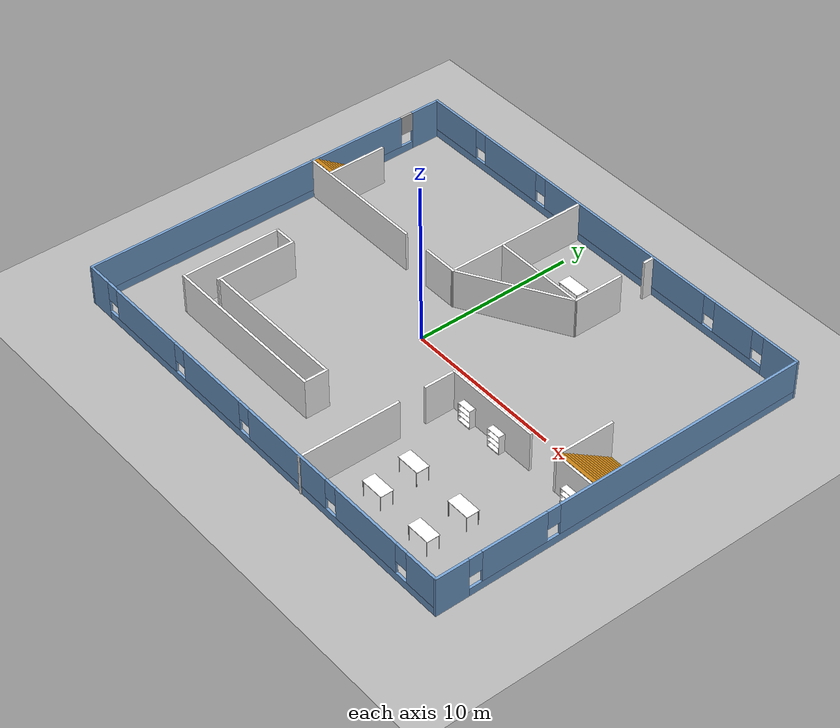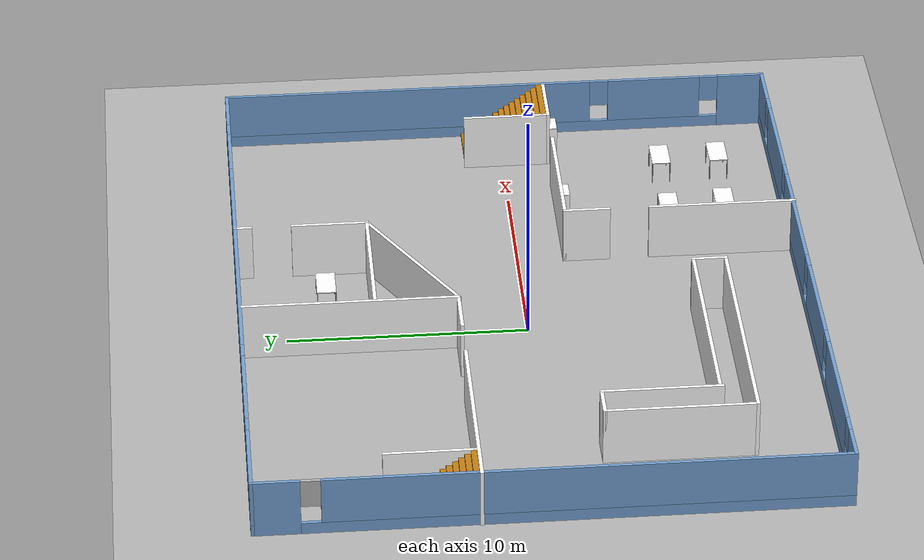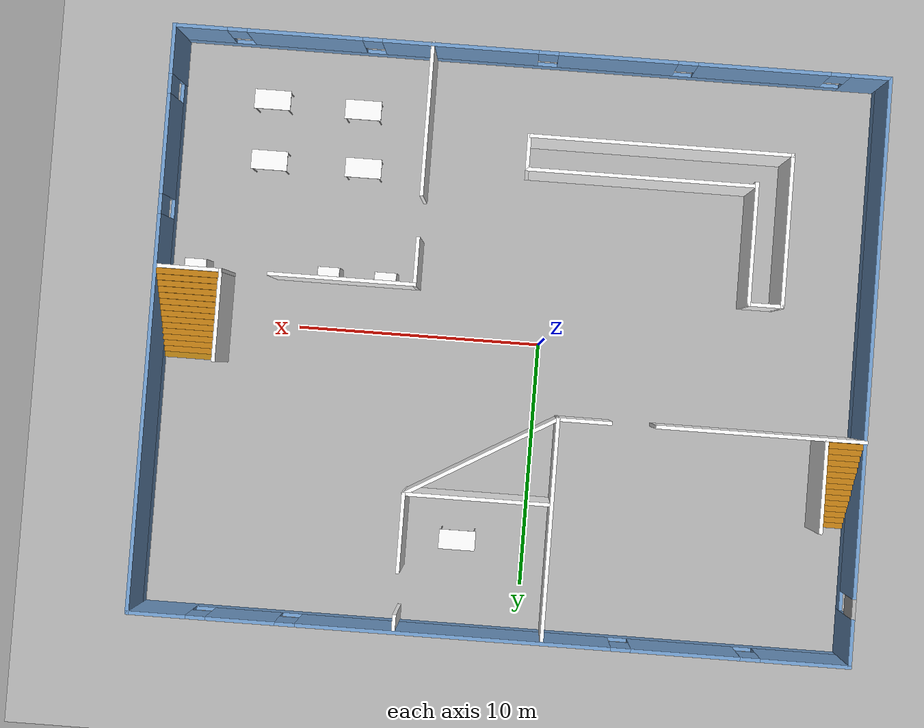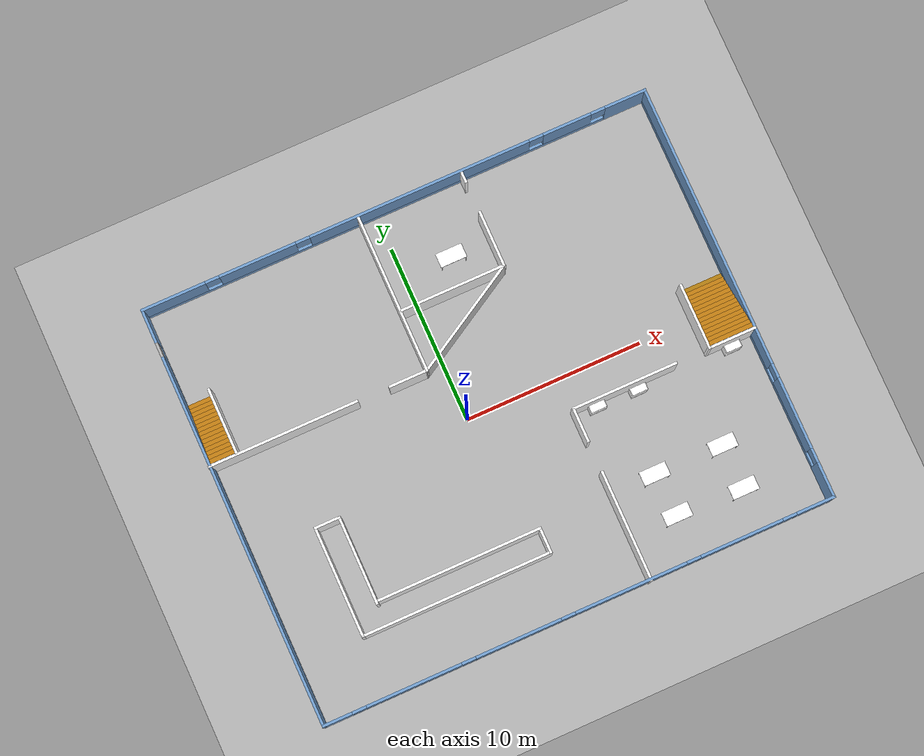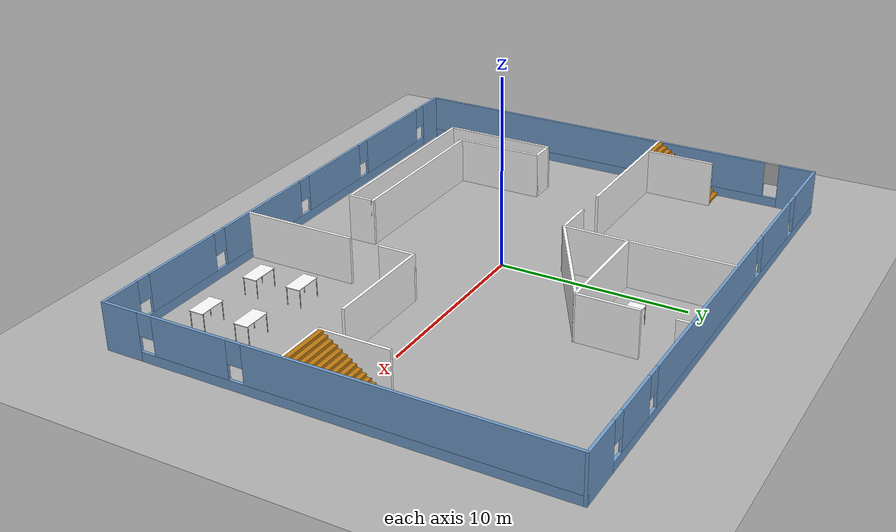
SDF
<sdf version="1.7">
 <world name="default">
  <physics name="1ms" type="ignored">
   <max_step_size>0.001</max_step_size>
   <real_time_factor>1.0</real_time_factor>
   <real_time_update_rate>1000</real_time_update_rate>
  </physics>
  <plugin filename="ignition-gazebo-physics-system" name="ignition::gazebo::systems::Physics"/>
  <plugin filename="ignition-gazebo-user-commands-system" name="ignition::gazebo::systems::UserCommands"/>
  <plugin filename="ignition-gazebo-scene-broadcaster-system" name="ignition::gazebo::systems::SceneBroadcaster"/>
  <plugin filename="libignition-gazebo-sensors-system.so" name="ignition::gazebo::systems::Sensors">
   <render_engine>ogre</render_engine>
  </plugin>
  <light name="sun" type="directional">
   <pose>0 0 10 0 -0 0</pose>
   <diffuse>0.8 0.8 0.8 1</diffuse>
   <specular>0.2 0.2 0.2 1</specular>
   <attenuation>
    <range>1000</range>
    <constant>0.9</constant>
    <linear>0.01</linear>
    <quadratic>0.001</quadratic>
   </attenuation>
   <direction>-0.5 0.1 -0.9</direction>
  </light>
  <model name="ground_plane">
   <static>1</static>
   <link name="link">
    <collision name="collision">
     <geometry><plane><normal>0 0 1</normal><size>100 100</size></plane></geometry>
     <surface>
      <contact><collide_bitmask>65535</collide_bitmask></contact>
      <friction><ode><mu>100</mu><mu2>50</mu2></ode></friction>
     </surface>
    </collision>
    <visual name="visual">
     <cast_shadows>0</cast_shadows>
     <geometry><plane><normal>0 0 1</normal><size>100 100</size></plane></geometry>
     <material>
      <ambient>0.7 0.7 0.7 1.0</ambient>
      <diffuse>0.7 0.7 0.7 1.0</diffuse>
      <specular>0.01 0.01 0.01 1.0</specular>
     </material>
    </visual>
   </link>
  </model>
  <gravity>0 0 -9.8</gravity>
  <magnetic_field>6e-06 2.3e-05 -4.2e-05</magnetic_field>
  <atmosphere type="adiabatic"/>
  <scene><ambient>0.4 0.4 0.4 1</ambient><background>0.7 0.7 0.7 1</background><shadows>1</shadows></scene>
  <model name="officeSpace1">
   <pose>1.12783 0.083294 0 0 -0 0</pose>
   <link name="Stairs_0">
    <visual name="Stairs_0_Visual_0">
     <pose>13.1278 1.44361 0.083333 0 -0 0</pose>
     <geometry><box><size>2.48543 0.236417 0.166667</size></box></geometry>
     <material>
      <ambient>0.7 0.490196 0.0666667 1</ambient>
      <diffuse>0.7 0.490196 0.0666667 1</diffuse>
      <specular>0.01 0.01 0.01 1.0</specular>
     </material>
     <meta><layer>0</layer></meta>
    </visual>
    <collision name="Stairs_0_Collision_0">
     <geometry><box><size>2.48543 0.236417 0.166667</size></box></geometry>
     <pose>13.1278 1.44361 0.083333 0 -0 0</pose>
    </collision>
    <visual name="Stairs_0_Visual_1">
     <pose>13.1278 1.20719 0.25 0 -0 0</pose>
     <geometry><box><size>2.48543 0.236417 0.166667</size></box></geometry>
     <material>
      <ambient>0.756863 0.490196 0.0666667 1</ambient>
      <diffuse>0.756863 0.490196 0.0666667 1</diffuse>
      <specular>0.01 0.01 0.01 1.0</specular>
     </material>
     <meta><layer>0</layer></meta>
    </visual>
    <collision name="Stairs_0_Collision_1">
     <geometry><box><size>2.48543 0.236417 0.166667</size></box></geometry>
     <pose>13.1278 1.20719 0.25 0 -0 0</pose>
    </collision>
    <visual name="Stairs_0_Visual_2">
     <pose>13.1278 0.97077 0.416667 0 -0 0</pose>
     <geometry><box><size>2.48543 0.236417 0.166667</size></box></geometry>
     <material>
      <ambient>0.756863 0.490196 0.0666667 1</ambient>
      <diffuse>0.756863 0.490196 0.0666667 1</diffuse>
      <specular>0.01 0.01 0.01 1.0</specular>
     </material>
     <meta><layer>0</layer></meta>
    </visual>
    <collision name="Stairs_0_Collision_2">
     <geometry><box><size>2.48543 0.236417 0.166667</size></box></geometry>
     <pose>13.1278 0.97077 0.416667 0 -0 0</pose>
    </collision>
    <visual name="Stairs_0_Visual_3">
     <pose>13.1278 0.734353 0.583333 0 -0 0</pose>
     <geometry><box><size>2.48543 0.236417 0.166667</size></box></geometry>
     <material>
      <ambient>0.756863 0.490196 0.0666667 1</ambient>
      <diffuse>0.756863 0.490196 0.0666667 1</diffuse>
      <specular>0.01 0.01 0.01 1.0</specular>
     </material>
     <meta><layer>0</layer></meta>
    </visual>
    <collision name="Stairs_0_Collision_3">
     <geometry><box><size>2.48543 0.236417 0.166667</size></box></geometry>
     <pose>13.1278 0.734353 0.583333 0 -0 0</pose>
    </collision>
    <visual name="Stairs_0_Visual_4">
     <pose>13.1278 0.497935 0.75 0 -0 0</pose>
     <geometry><box><size>2.48543 0.236417 0.166667</size></box></geometry>
     <material>
      <ambient>0.756863 0.490196 0.0666667 1</ambient>
      <diffuse>0.756863 0.490196 0.0666667 1</diffuse>
      <specular>0.01 0.01 0.01 1.0</specular>
     </material>
     <meta><layer>0</layer></meta>
    </visual>
    <collision name="Stairs_0_Collision_4">
     <geometry><box><size>2.48543 0.236417 0.166667</size></box></geometry>
     <pose>13.1278 0.497935 0.75 0 -0 0</pose>
    </collision>
    <visual name="Stairs_0_Visual_5">
     <pose>13.1278 0.261518 0.916667 0 -0 0</pose>
     <geometry><box><size>2.48543 0.236417 0.166667</size></box></geometry>
     <material>
      <ambient>0.756863 0.490196 0.0666667 1</ambient>
      <diffuse>0.756863 0.490196 0.0666667 1</diffuse>
      <specular>0.01 0.01 0.01 1.0</specular>
     </material>
     <meta><layer>0</layer></meta>
    </visual>
    <collision name="Stairs_0_Collision_5">
     <geometry><box><size>2.48543 0.236417 0.166667</size></box></geometry>
     <pose>13.1278 0.261518 0.916667 0 -0 0</pose>
    </collision>
    <visual name="Stairs_0_Visual_6">
     <pose>13.1278 0.0251 1.08333 0 -0 0</pose>
     <geometry><box><size>2.48543 0.236417 0.166667</size></box></geometry>
     <material>
      <ambient>0.756863 0.490196 0.0666667 1</ambient>
      <diffuse>0.756863 0.490196 0.0666667 1</diffuse>
      <specular>0.01 0.01 0.01 1.0</specular>
     </material>
     <meta><layer>0</layer></meta>
    </visual>
    <collision name="Stairs_0_Collision_6">
     <geometry><box><size>2.48543 0.236417 0.166667</size></box></geometry>
     <pose>13.1278 0.0251 1.08333 0 -0 0</pose>
    </collision>
    <visual name="Stairs_0_Visual_7">
     <pose>13.1278 -0.211317 1.25 0 -0 0</pose>
     <geometry><box><size>2.48543 0.236417 0.166667</size></box></geometry>
     <material>
      <ambient>0.756863 0.490196 0.0666667 1</ambient>
      <diffuse>0.756863 0.490196 0.0666667 1</diffuse>
      <specular>0.01 0.01 0.01 1.0</specular>
     </material>
     <meta><layer>0</layer></meta>
    </visual>
    <collision name="Stairs_0_Collision_7">
     <geometry><box><size>2.48543 0.236417 0.166667</size></box></geometry>
     <pose>13.1278 -0.211317 1.25 0 -0 0</pose>
    </collision>
    <visual name="Stairs_0_Visual_8">
     <pose>13.1278 -0.447735 1.41667 0 -0 0</pose>
     <geometry><box><size>2.48543 0.236417 0.166667</size></box></geometry>
     <material>
      <ambient>0.756863 0.490196 0.0666667 1</ambient>
      <diffuse>0.756863 0.490196 0.0666667 1</diffuse>
      <specular>0.01 0.01 0.01 1.0</specular>
     </material>
     <meta><layer>0</layer></meta>
    </visual>
    <collision name="Stairs_0_Collision_8">
     <geometry><box><size>2.48543 0.236417 0.166667</size></box></geometry>
     <pose>13.1278 -0.447735 1.41667 0 -0 0</pose>
    </collision>
    <visual name="Stairs_0_Visual_9">
     <pose>13.1278 -0.684152 1.58333 0 -0 0</pose>
     <geometry><box><size>2.48543 0.236417 0.166667</size></box></geometry>
     <material>
      <ambient>0.756863 0.490196 0.0666667 1</ambient>
      <diffuse>0.756863 0.490196 0.0666667 1</diffuse>
      <specular>0.01 0.01 0.01 1.0</specular>
     </material>
     <meta><layer>0</layer></meta>
    </visual>
    <collision name="Stairs_0_Collision_9">
     <geometry><box><size>2.48543 0.236417 0.166667</size></box></geometry>
     <pose>13.1278 -0.684152 1.58333 0 -0 0</pose>
    </collision>
    <visual name="Stairs_0_Visual_10">
     <pose>13.1278 -0.920569 1.75 0 -0 0</pose>
     <geometry><box><size>2.48543 0.236417 0.166667</size></box></geometry>
     <material>
      <ambient>0.756863 0.490196 0.0666667 1</ambient>
      <diffuse>0.756863 0.490196 0.0666667 1</diffuse>
      <specular>0.01 0.01 0.01 1.0</specular>
     </material>
     <meta><layer>0</layer></meta>
    </visual>
    <collision name="Stairs_0_Collision_10">
     <geometry><box><size>2.48543 0.236417 0.166667</size></box></geometry>
     <pose>13.1278 -0.920569 1.75 0 -0 0</pose>
    </collision>
    <visual name="Stairs_0_Visual_11">
     <pose>13.1278 -1.15699 1.91667 0 -0 0</pose>
     <geometry><box><size>2.48543 0.236417 0.166667</size></box></geometry>
     <material>
      <ambient>0.756863 0.490196 0.0666667 1</ambient>
      <diffuse>0.756863 0.490196 0.0666667 1</diffuse>
      <specular>0.01 0.01 0.01 1.0</specular>
     </material>
     <meta><layer>0</layer></meta>
    </visual>
    <collision name="Stairs_0_Collision_11">
     <geometry><box><size>2.48543 0.236417 0.166667</size></box></geometry>
     <pose>13.1278 -1.15699 1.91667 0 -0 0</pose>
    </collision>
    <visual name="Stairs_0_Visual_12">
     <pose>13.1278 -1.3934 2.08333 0 -0 0</pose>
     <geometry><box><size>2.48543 0.236417 0.166667</size></box></geometry>
     <material>
      <ambient>0.756863 0.490196 0.0666667 1</ambient>
      <diffuse>0.756863 0.490196 0.0666667 1</diffuse>
      <specular>0.01 0.01 0.01 1.0</specular>
     </material>
     <meta><layer>0</layer></meta>
    </visual>
    <collision name="Stairs_0_Collision_12">
     <geometry><box><size>2.48543 0.236417 0.166667</size></box></geometry>
     <pose>13.1278 -1.3934 2.08333 0 -0 0</pose>
    </collision>
    <visual name="Stairs_0_Visual_13">
     <pose>13.1278 -1.62982 2.25 0 -0 0</pose>
     <geometry><box><size>2.48543 0.236417 0.166667</size></box></geometry>
     <material>
      <ambient>0.756863 0.490196 0.0666667 1</ambient>
      <diffuse>0.756863 0.490196 0.0666667 1</diffuse>
      <specular>0.01 0.01 0.01 1.0</specular>
     </material>
     <meta><layer>0</layer></meta>
    </visual>
    <collision name="Stairs_0_Collision_13">
     <geometry><box><size>2.48543 0.236417 0.166667</size></box></geometry>
     <pose>13.1278 -1.62982 2.25 0 -0 0</pose>
    </collision>
    <visual name="Stairs_0_Visual_14">
     <pose>13.1278 -1.86624 2.41667 0 -0 0</pose>
     <geometry><box><size>2.48543 0.236417 0.166667</size></box></geometry>
     <material>
      <ambient>0.756863 0.490196 0.0666667 1</ambient>
      <diffuse>0.756863 0.490196 0.0666667 1</diffuse>
      <specular>0.01 0.01 0.01 1.0</specular>
     </material>
     <meta><layer>0</layer></meta>
    </visual>
    <collision name="Stairs_0_Collision_14">
     <geometry><box><size>2.48543 0.236417 0.166667</size></box></geometry>
     <pose>13.1278 -1.86624 2.41667 0 -0 0</pose>
    </collision>
   </link>
   <link name="Stairs_1">
    <visual name="Stairs_1_Visual_0">
     <pose>-13.6441 6.47079 0.083333 0 -0 0</pose>
     <geometry><box><size>1.37009 0.242586 0.166667</size></box></geometry>
     <material>
      <ambient>0.756863 0.490196 0.0666667 1</ambient>
      <diffuse>0.756863 0.490196 0.0666667 1</diffuse>
      <specular>0.01 0.01 0.01 1.0</specular>
     </material>
     <meta><layer>0</layer></meta>
    </visual>
    <collision name="Stairs_1_Collision_0">
     <geometry><box><size>1.37009 0.242586 0.166667</size></box></geometry>
     <pose>-13.6441 6.47079 0.083333 0 -0 0</pose>
    </collision>
    <visual name="Stairs_1_Visual_1">
     <pose>-13.6441 6.2282 0.25 0 -0 0</pose>
     <geometry><box><size>1.37009 0.242586 0.166667</size></box></geometry>
     <material>
      <ambient>0.756863 0.490196 0.0666667 1</ambient>
      <diffuse>0.756863 0.490196 0.0666667 1</diffuse>
      <specular>0.01 0.01 0.01 1.0</specular>
     </material>
     <meta><layer>0</layer></meta>
    </visual>
    <collision name="Stairs_1_Collision_1">
     <geometry><box><size>1.37009 0.242586 0.166667</size></box></geometry>
     <pose>-13.6441 6.2282 0.25 0 -0 0</pose>
    </collision>
    <visual name="Stairs_1_Visual_2">
     <pose>-13.6441 5.98562 0.416667 0 -0 0</pose>
     <geometry><box><size>1.37009 0.242586 0.166667</size></box></geometry>
     <material>
      <ambient>0.756863 0.490196 0.0666667 1</ambient>
      <diffuse>0.756863 0.490196 0.0666667 1</diffuse>
      <specular>0.01 0.01 0.01 1.0</specular>
     </material>
     <meta><layer>0</layer></meta>
    </visual>
    <collision name="Stairs_1_Collision_2">
     <geometry><box><size>1.37009 0.242586 0.166667</size></box></geometry>
     <pose>-13.6441 5.98562 0.416667 0 -0 0</pose>
    </collision>
    <visual name="Stairs_1_Visual_3">
     <pose>-13.6441 5.74303 0.583333 0 -0 0</pose>
     <geometry><box><size>1.37009 0.242586 0.166667</size></box></geometry>
     <material>
      <ambient>0.756863 0.490196 0.0666667 1</ambient>
      <diffuse>0.756863 0.490196 0.0666667 1</diffuse>
      <specular>0.01 0.01 0.01 1.0</specular>
     </material>
     <meta><layer>0</layer></meta>
    </visual>
    <collision name="Stairs_1_Collision_3">
     <geometry><box><size>1.37009 0.242586 0.166667</size></box></geometry>
     <pose>-13.6441 5.74303 0.583333 0 -0 0</pose>
    </collision>
    <visual name="Stairs_1_Visual_4">
     <pose>-13.6441 5.50045 0.75 0 -0 0</pose>
     <geometry><box><size>1.37009 0.242586 0.166667</size></box></geometry>
     <material>
      <ambient>0.756863 0.490196 0.0666667 1</ambient>
      <diffuse>0.756863 0.490196 0.0666667 1</diffuse>
      <specular>0.01 0.01 0.01 1.0</specular>
     </material>
     <meta><layer>0</layer></meta>
    </visual>
    <collision name="Stairs_1_Collision_4">
     <geometry><box><size>1.37009 0.242586 0.166667</size></box></geometry>
     <pose>-13.6441 5.50045 0.75 0 -0 0</pose>
    </collision>
    <visual name="Stairs_1_Visual_5">
     <pose>-13.6441 5.25786 0.916667 0 -0 0</pose>
     <geometry><box><size>1.37009 0.242586 0.166667</size></box></geometry>
     <material>
      <ambient>0.756863 0.490196 0.0666667 1</ambient>
      <diffuse>0.756863 0.490196 0.0666667 1</diffuse>
      <specular>0.01 0.01 0.01 1.0</specular>
     </material>
     <meta><layer>0</layer></meta>
    </visual>
    <collision name="Stairs_1_Collision_5">
     <geometry><box><size>1.37009 0.242586 0.166667</size></box></geometry>
     <pose>-13.6441 5.25786 0.916667 0 -0 0</pose>
    </collision>
    <visual name="Stairs_1_Visual_6">
     <pose>-13.6441 5.01528 1.08333 0 -0 0</pose>
     <geometry><box><size>1.37009 0.242586 0.166667</size></box></geometry>
     <material>
      <ambient>0.756863 0.490196 0.0666667 1</ambient>
      <diffuse>0.756863 0.490196 0.0666667 1</diffuse>
      <specular>0.01 0.01 0.01 1.0</specular>
     </material>
     <meta><layer>0</layer></meta>
    </visual>
    <collision name="Stairs_1_Collision_6">
     <geometry><box><size>1.37009 0.242586 0.166667</size></box></geometry>
     <pose>-13.6441 5.01528 1.08333 0 -0 0</pose>
    </collision>
    <visual name="Stairs_1_Visual_7">
     <pose>-13.6441 4.77269 1.25 0 -0 0</pose>
     <geometry><box><size>1.37009 0.242586 0.166667</size></box></geometry>
     <material>
      <ambient>0.756863 0.490196 0.0666667 1</ambient>
      <diffuse>0.756863 0.490196 0.0666667 1</diffuse>
      <specular>0.01 0.01 0.01 1.0</specular>
     </material>
     <meta><layer>0</layer></meta>
    </visual>
    <collision name="Stairs_1_Collision_7">
     <geometry><box><size>1.37009 0.242586 0.166667</size></box></geometry>
     <pose>-13.6441 4.77269 1.25 0 -0 0</pose>
    </collision>
    <visual name="Stairs_1_Visual_8">
     <pose>-13.6441 4.53011 1.41667 0 -0 0</pose>
     <geometry><box><size>1.37009 0.242586 0.166667</size></box></geometry>
     <material>
      <ambient>0.756863 0.490196 0.0666667 1</ambient>
      <diffuse>0.756863 0.490196 0.0666667 1</diffuse>
      <specular>0.01 0.01 0.01 1.0</specular>
     </material>
     <meta><layer>0</layer></meta>
    </visual>
    <collision name="Stairs_1_Collision_8">
     <geometry><box><size>1.37009 0.242586 0.166667</size></box></geometry>
     <pose>-13.6441 4.53011 1.41667 0 -0 0</pose>
    </collision>
    <visual name="Stairs_1_Visual_9">
     <pose>-13.6441 4.28752 1.58333 0 -0 0</pose>
     <geometry><box><size>1.37009 0.242586 0.166667</size></box></geometry>
     <material>
      <ambient>0.756863 0.490196 0.0666667 1</ambient>
      <diffuse>0.756863 0.490196 0.0666667 1</diffuse>
      <specular>0.01 0.01 0.01 1.0</specular>
     </material>
     <meta><layer>0</layer></meta>
    </visual>
    <collision name="Stairs_1_Collision_9">
     <geometry><box><size>1.37009 0.242586 0.166667</size></box></geometry>
     <pose>-13.6441 4.28752 1.58333 0 -0 0</pose>
    </collision>
    <visual name="Stairs_1_Visual_10">
     <pose>-13.6441 4.04493 1.75 0 -0 0</pose>
     <geometry><box><size>1.37009 0.242586 0.166667</size></box></geometry>
     <material>
      <ambient>0.756863 0.490196 0.0666667 1</ambient>
      <diffuse>0.756863 0.490196 0.0666667 1</diffuse>
      <specular>0.01 0.01 0.01 1.0</specular>
     </material>
     <meta><layer>0</layer></meta>
    </visual>
    <collision name="Stairs_1_Collision_10">
     <geometry><box><size>1.37009 0.242586 0.166667</size></box></geometry>
     <pose>-13.6441 4.04493 1.75 0 -0 0</pose>
    </collision>
    <visual name="Stairs_1_Visual_11">
     <pose>-13.6441 3.80235 1.91667 0 -0 0</pose>
     <geometry><box><size>1.37009 0.242586 0.166667</size></box></geometry>
     <material>
      <ambient>0.756863 0.490196 0.0666667 1</ambient>
      <diffuse>0.756863 0.490196 0.0666667 1</diffuse>
      <specular>0.01 0.01 0.01 1.0</specular>
     </material>
     <meta><layer>0</layer></meta>
    </visual>
    <collision name="Stairs_1_Collision_11">
     <geometry><box><size>1.37009 0.242586 0.166667</size></box></geometry>
     <pose>-13.6441 3.80235 1.91667 0 -0 0</pose>
    </collision>
    <visual name="Stairs_1_Visual_12">
     <pose>-13.6441 3.55976 2.08333 0 -0 0</pose>
     <geometry><box><size>1.37009 0.242586 0.166667</size></box></geometry>
     <material>
      <ambient>0.756863 0.490196 0.0666667 1</ambient>
      <diffuse>0.756863 0.490196 0.0666667 1</diffuse>
      <specular>0.01 0.01 0.01 1.0</specular>
     </material>
     <meta><layer>0</layer></meta>
    </visual>
    <collision name="Stairs_1_Collision_12">
     <geometry><box><size>1.37009 0.242586 0.166667</size></box></geometry>
     <pose>-13.6441 3.55976 2.08333 0 -0 0</pose>
    </collision>
    <visual name="Stairs_1_Visual_13">
     <pose>-13.6441 3.31718 2.25 0 -0 0</pose>
     <geometry><box><size>1.37009 0.242586 0.166667</size></box></geometry>
     <material>
      <ambient>0.756863 0.490196 0.0666667 1</ambient>
      <diffuse>0.756863 0.490196 0.0666667 1</diffuse>
      <specular>0.01 0.01 0.01 1.0</specular>
     </material>
     <meta><layer>0</layer></meta>
    </visual>
    <collision name="Stairs_1_Collision_13">
     <geometry><box><size>1.37009 0.242586 0.166667</size></box></geometry>
     <pose>-13.6441 3.31718 2.25 0 -0 0</pose>
    </collision>
    <visual name="Stairs_1_Visual_14">
     <pose>-13.6441 3.07459 2.41667 0 -0 0</pose>
     <geometry><box><size>1.37009 0.242586 0.166667</size></box></geometry>
     <material>
      <ambient>0.756863 0.490196 0.0666667 1</ambient>
      <diffuse>0.756863 0.490196 0.0666667 1</diffuse>
      <specular>0.01 0.01 0.01 1.0</specular>
     </material>
     <meta><layer>0</layer></meta>
    </visual>
    <collision name="Stairs_1_Collision_14">
     <geometry><box><size>1.37009 0.242586 0.166667</size></box></geometry>
     <pose>-13.6441 3.07459 2.41667 0 -0 0</pose>
    </collision>
   </link>
   <link name="Wall_15">
    <pose>0.019773 -11.7779 0 0 -0 0</pose>
    <visual name="Wall_15_Visual_0">
     <pose>-13.6565 0 1.25 0 -0 0</pose>
     <geometry><box><size>1.68692 0.15 2.5</size></box></geometry>
     <material>
      <ambient>0.447059 0.623529 0.811765 1</ambient>
      <diffuse>0.447059 0.623529 0.811765 1</diffuse>
      <specular>0.01 0.01 0.01 1.0</specular>
     </material>
     <meta><layer>0</layer></meta>
    </visual>
    <collision name="Wall_15_Collision_0">
     <geometry><box><size>1.68692 0.15 2.5</size></box></geometry>
     <pose>-13.6565 0 1.25 0 -0 0</pose>
    </collision>
    <visual name="Wall_15_Visual_1">
     <pose>0.84346 0 0.25 0 -0 0</pose>
     <geometry><box><size>27.3131 0.15 0.5</size></box></geometry>
     <material>
      <ambient>0.447059 0.623529 0.811765 1</ambient>
      <diffuse>0.447059 0.623529 0.811765 1</diffuse>
      <specular>0.01 0.01 0.01 1.0</specular>
     </material>
     <meta><layer>0</layer></meta>
    </visual>
    <collision name="Wall_15_Collision_1">
     <geometry><box><size>27.3131 0.15 0.5</size></box></geometry>
     <pose>0.84346 0 0.25 0 -0 0</pose>
    </collision>
    <visual name="Wall_15_Visual_2">
     <pose>-9.34337 0 1.5 0 -0 0</pose>
     <geometry><box><size>5.33941 0.15 2</size></box></geometry>
     <material>
      <ambient>0.447059 0.623529 0.811765 1</ambient>
      <diffuse>0.447059 0.623529 0.811765 1</diffuse>
      <specular>0.01 0.01 0.01 1.0</specular>
     </material>
     <meta><layer>0</layer></meta>
    </visual>
    <collision name="Wall_15_Collision_2">
     <geometry><box><size>5.33941 0.15 2</size></box></geometry>
     <pose>-9.34337 0 1.5 0 -0 0</pose>
    </collision>
    <visual name="Wall_15_Visual_3">
     <pose>-3.46479 0 1.5 0 -0 0</pose>
     <geometry><box><size>4.81776 0.15 2</size></box></geometry>
     <material>
      <ambient>0.447059 0.623529 0.811765 1</ambient>
      <diffuse>0.447059 0.623529 0.811765 1</diffuse>
      <specular>0.01 0.01 0.01 1.0</specular>
     </material>
     <meta><layer>0</layer></meta>
    </visual>
    <collision name="Wall_15_Collision_3">
     <geometry><box><size>4.81776 0.15 2</size></box></geometry>
     <pose>-3.46479 0 1.5 0 -0 0</pose>
    </collision>
    <visual name="Wall_15_Visual_4">
     <pose>2.89532 0 1.5 0 -0 0</pose>
     <geometry><box><size>6.30246 0.15 2</size></box></geometry>
     <material>
      <ambient>0.447059 0.623529 0.811765 1</ambient>
      <diffuse>0.447059 0.623529 0.811765 1</diffuse>
      <specular>0.01 0.01 0.01 1.0</specular>
     </material>
     <meta><layer>0</layer></meta>
    </visual>
    <collision name="Wall_15_Collision_4">
     <geometry><box><size>6.30246 0.15 2</size></box></geometry>
     <pose>2.89532 0 1.5 0 -0 0</pose>
    </collision>
    <visual name="Wall_15_Visual_5">
     <pose>9.17518 0 1.5 0 -0 0</pose>
     <geometry><box><size>4.65726 0.15 2</size></box></geometry>
     <material>
      <ambient>0.447059 0.623529 0.811765 1</ambient>
      <diffuse>0.447059 0.623529 0.811765 1</diffuse>
      <specular>0.01 0.01 0.01 1.0</specular>
     </material>
     <meta><layer>0</layer></meta>
    </visual>
    <collision name="Wall_15_Collision_5">
     <geometry><box><size>4.65726 0.15 2</size></box></geometry>
     <pose>9.17518 0 1.5 0 -0 0</pose>
    </collision>
    <visual name="Wall_15_Visual_6">
     <pose>13.4019 0 1.5 0 -0 0</pose>
     <geometry><box><size>2.19619 0.15 2</size></box></geometry>
     <material>
      <ambient>0.447059 0.623529 0.811765 1</ambient>
      <diffuse>0.447059 0.623529 0.811765 1</diffuse>
      <specular>0.01 0.01 0.01 1.0</specular>
     </material>
     <meta><layer>0</layer></meta>
    </visual>
    <collision name="Wall_15_Collision_6">
     <geometry><box><size>2.19619 0.15 2</size></box></geometry>
     <pose>13.4019 0 1.5 0 -0 0</pose>
    </collision>
    <visual name="Wall_15_Visual_7">
     <pose>-12.4131 0 1.9 0 -0 0</pose>
     <geometry><box><size>0.8 0.15 1.2</size></box></geometry>
     <material>
      <ambient>0.447059 0.623529 0.811765 1</ambient>
      <diffuse>0.447059 0.623529 0.811765 1</diffuse>
      <specular>0.01 0.01 0.01 1.0</specular>
     </material>
     <meta><layer>0</layer></meta>
    </visual>
    <collision name="Wall_15_Collision_7">
     <geometry><box><size>0.8 0.15 1.2</size></box></geometry>
     <pose>-12.4131 0 1.9 0 -0 0</pose>
    </collision>
    <visual name="Wall_15_Visual_8">
     <pose>-6.27367 0 1.9 0 -0 0</pose>
     <geometry><box><size>0.8 0.15 1.2</size></box></geometry>
     <material>
      <ambient>0.447059 0.623529 0.811765 1</ambient>
      <diffuse>0.447059 0.623529 0.811765 1</diffuse>
      <specular>0.01 0.01 0.01 1.0</specular>
     </material>
     <meta><layer>0</layer></meta>
    </visual>
    <collision name="Wall_15_Collision_8">
     <geometry><box><size>0.8 0.15 1.2</size></box></geometry>
     <pose>-6.27367 0 1.9 0 -0 0</pose>
    </collision>
    <visual name="Wall_15_Visual_9">
     <pose>-0.655904 0 1.9 0 -0 0</pose>
     <geometry><box><size>0.8 0.15 1.2</size></box></geometry>
     <material>
      <ambient>0.447059 0.623529 0.811765 1</ambient>
      <diffuse>0.447059 0.623529 0.811765 1</diffuse>
      <specular>0.01 0.01 0.01 1.0</specular>
     </material>
     <meta><layer>0</layer></meta>
    </visual>
    <collision name="Wall_15_Collision_9">
     <geometry><box><size>0.8 0.15 1.2</size></box></geometry>
     <pose>-0.655904 0 1.9 0 -0 0</pose>
    </collision>
    <visual name="Wall_15_Visual_10">
     <pose>6.44655 0 1.9 0 -0 0</pose>
     <geometry><box><size>0.8 0.15 1.2</size></box></geometry>
     <material>
      <ambient>0.447059 0.623529 0.811765 1</ambient>
      <diffuse>0.447059 0.623529 0.811765 1</diffuse>
      <specular>0.01 0.01 0.01 1.0</specular>
     </material>
     <meta><layer>0</layer></meta>
    </visual>
    <collision name="Wall_15_Collision_10">
     <geometry><box><size>0.8 0.15 1.2</size></box></geometry>
     <pose>6.44655 0 1.9 0 -0 0</pose>
    </collision>
    <visual name="Wall_15_Visual_11">
     <pose>11.9038 0 1.9 0 -0 0</pose>
     <geometry><box><size>0.8 0.15 1.2</size></box></geometry>
     <material>
      <ambient>0.447059 0.623529 0.811765 1</ambient>
      <diffuse>0.447059 0.623529 0.811765 1</diffuse>
      <specular>0.01 0.01 0.01 1.0</specular>
     </material>
     <meta><layer>0</layer></meta>
    </visual>
    <collision name="Wall_15_Collision_11">
     <geometry><box><size>0.8 0.15 1.2</size></box></geometry>
     <pose>11.9038 0 1.9 0 -0 0</pose>
    </collision>
   </link>
   <link name="Wall_16">
    <pose>14.4448 0.022067 0 0 -0 1.5708</pose>
    <visual name="Wall_16_Visual_0">
     <pose>-10.8556 0 1.25 0 -0 0</pose>
     <geometry><box><size>2.03884 0.15 2.5</size></box></geometry>
     <material>
      <ambient>0.447059 0.623529 0.811765 1</ambient>
      <diffuse>0.447059 0.623529 0.811765 1</diffuse>
      <specular>0.01 0.01 0.01 1.0</specular>
     </material>
     <meta><layer>0</layer></meta>
    </visual>
    <collision name="Wall_16_Collision_0">
     <geometry><box><size>2.03884 0.15 2.5</size></box></geometry>
     <pose>-10.8556 0 1.25 0 -0 0</pose>
    </collision>
    <visual name="Wall_16_Visual_1">
     <pose>1.01942 0 0.25 0 -0 0</pose>
     <geometry><box><size>21.7112 0.15 0.5</size></box></geometry>
     <material>
      <ambient>0.447059 0.623529 0.811765 1</ambient>
      <diffuse>0.447059 0.623529 0.811765 1</diffuse>
      <specular>0.01 0.01 0.01 1.0</specular>
     </material>
     <meta><layer>0</layer></meta>
    </visual>
    <collision name="Wall_16_Collision_1">
     <geometry><box><size>21.7112 0.15 0.5</size></box></geometry>
     <pose>1.01942 0 0.25 0 -0 0</pose>
    </collision>
    <visual name="Wall_16_Visual_2">
     <pose>-7.00849 0 1.5 0 -0 0</pose>
     <geometry><box><size>4.05535 0.15 2</size></box></geometry>
     <material>
      <ambient>0.447059 0.623529 0.811765 1</ambient>
      <diffuse>0.447059 0.623529 0.811765 1</diffuse>
      <specular>0.01 0.01 0.01 1.0</specular>
     </material>
     <meta><layer>0</layer></meta>
    </visual>
    <collision name="Wall_16_Collision_2">
     <geometry><box><size>4.05535 0.15 2</size></box></geometry>
     <pose>-7.00849 0 1.5 0 -0 0</pose>
    </collision>
    <visual name="Wall_16_Visual_3">
     <pose>3.84709 0 1.5 0 -0 0</pose>
     <geometry><box><size>16.0558 0.15 2</size></box></geometry>
     <material>
      <ambient>0.447059 0.623529 0.811765 1</ambient>
      <diffuse>0.447059 0.623529 0.811765 1</diffuse>
      <specular>0.01 0.01 0.01 1.0</specular>
     </material>
     <meta><layer>0</layer></meta>
    </visual>
    <collision name="Wall_16_Collision_3">
     <geometry><box><size>16.0558 0.15 2</size></box></geometry>
     <pose>3.84709 0 1.5 0 -0 0</pose>
    </collision>
    <visual name="Wall_16_Visual_4">
     <pose>-9.43617 0 1.9 0 -0 0</pose>
     <geometry><box><size>0.8 0.15 1.2</size></box></geometry>
     <material>
      <ambient>0.447059 0.623529 0.811765 1</ambient>
      <diffuse>0.447059 0.623529 0.811765 1</diffuse>
      <specular>0.01 0.01 0.01 1.0</specular>
     </material>
     <meta><layer>0</layer></meta>
    </visual>
    <collision name="Wall_16_Collision_4">
     <geometry><box><size>0.8 0.15 1.2</size></box></geometry>
     <pose>-9.43617 0 1.9 0 -0 0</pose>
    </collision>
    <visual name="Wall_16_Visual_5">
     <pose>-4.58081 0 1.9 0 -0 0</pose>
     <geometry><box><size>0.8 0.15 1.2</size></box></geometry>
     <material>
      <ambient>0.447059 0.623529 0.811765 1</ambient>
      <diffuse>0.447059 0.623529 0.811765 1</diffuse>
      <specular>0.01 0.01 0.01 1.0</specular>
     </material>
     <meta><layer>0</layer></meta>
    </visual>
    <collision name="Wall_16_Collision_5">
     <geometry><box><size>0.8 0.15 1.2</size></box></geometry>
     <pose>-4.58081 0 1.9 0 -0 0</pose>
    </collision>
   </link>
   <link name="Wall_17">
    <pose>0.019773 11.8221 0 0 -0 3.14159</pose>
    <visual name="Wall_17_Visual_0">
     <pose>-13.3016 0 1.25 0 -0 0</pose>
     <geometry><box><size>2.39683 0.15 2.5</size></box></geometry>
     <material>
      <ambient>0.447059 0.623529 0.811765 1</ambient>
      <diffuse>0.447059 0.623529 0.811765 1</diffuse>
      <specular>0.01 0.01 0.01 1.0</specular>
     </material>
     <meta><layer>0</layer></meta>
    </visual>
    <collision name="Wall_17_Collision_0">
     <geometry><box><size>2.39683 0.15 2.5</size></box></geometry>
     <pose>-13.3016 0 1.25 0 -0 0</pose>
    </collision>
    <visual name="Wall_17_Visual_1">
     <pose>1.19841 0 0.25 0 -0 0</pose>
     <geometry><box><size>26.6032 0.15 0.5</size></box></geometry>
     <material>
      <ambient>0.447059 0.623529 0.811765 1</ambient>
      <diffuse>0.447059 0.623529 0.811765 1</diffuse>
      <specular>0.01 0.01 0.01 1.0</specular>
     </material>
     <meta><layer>0</layer></meta>
    </visual>
    <collision name="Wall_17_Collision_1">
     <geometry><box><size>26.6032 0.15 0.5</size></box></geometry>
     <pose>1.19841 0 0.25 0 -0 0</pose>
    </collision>
    <visual name="Wall_17_Visual_2">
     <pose>-9.91753 0 1.5 0 -0 0</pose>
     <geometry><box><size>2.77129 0.15 2</size></box></geometry>
     <material>
      <ambient>0.447059 0.623529 0.811765 1</ambient>
      <diffuse>0.447059 0.623529 0.811765 1</diffuse>
      <specular>0.01 0.01 0.01 1.0</specular>
     </material>
     <meta><layer>0</layer></meta>
    </visual>
    <collision name="Wall_17_Collision_2">
     <geometry><box><size>2.77129 0.15 2</size></box></geometry>
     <pose>-9.91753 0 1.5 0 -0 0</pose>
    </collision>
    <visual name="Wall_17_Visual_3">
     <pose>-1.42429 0 1.5 0 -0 0</pose>
     <geometry><box><size>12.6152 0.15 2</size></box></geometry>
     <material>
      <ambient>0.447059 0.623529 0.811765 1</ambient>
      <diffuse>0.447059 0.623529 0.811765 1</diffuse>
      <specular>0.01 0.01 0.01 1.0</specular>
     </material>
     <meta><layer>0</layer></meta>
    </visual>
    <collision name="Wall_17_Collision_3">
     <geometry><box><size>12.6152 0.15 2</size></box></geometry>
     <pose>-1.42429 0 1.5 0 -0 0</pose>
    </collision>
    <visual name="Wall_17_Visual_4">
     <pose>7.86509 0 1.5 0 -0 0</pose>
     <geometry><box><size>4.36355 0.15 2</size></box></geometry>
     <material>
      <ambient>0.447059 0.623529 0.811765 1</ambient>
      <diffuse>0.447059 0.623529 0.811765 1</diffuse>
      <specular>0.01 0.01 0.01 1.0</specular>
     </material>
     <meta><layer>0</layer></meta>
    </visual>
    <collision name="Wall_17_Collision_4">
     <geometry><box><size>4.36355 0.15 2</size></box></geometry>
     <pose>7.86509 0 1.5 0 -0 0</pose>
    </collision>
    <visual name="Wall_17_Visual_5">
     <pose>12.6734 0 1.5 0 -0 0</pose>
     <geometry><box><size>3.65314 0.15 2</size></box></geometry>
     <material>
      <ambient>0.447059 0.623529 0.811765 1</ambient>
      <diffuse>0.447059 0.623529 0.811765 1</diffuse>
      <specular>0.01 0.01 0.01 1.0</specular>
     </material>
     <meta><layer>0</layer></meta>
    </visual>
    <collision name="Wall_17_Collision_5">
     <geometry><box><size>3.65314 0.15 2</size></box></geometry>
     <pose>12.6734 0 1.5 0 -0 0</pose>
    </collision>
    <visual name="Wall_17_Visual_6">
     <pose>-11.7032 0 1.9 0 -0 0</pose>
     <geometry><box><size>0.8 0.15 1.2</size></box></geometry>
     <material>
      <ambient>0.447059 0.623529 0.811765 1</ambient>
      <diffuse>0.447059 0.623529 0.811765 1</diffuse>
      <specular>0.01 0.01 0.01 1.0</specular>
     </material>
     <meta><layer>0</layer></meta>
    </visual>
    <collision name="Wall_17_Collision_6">
     <geometry><box><size>0.8 0.15 1.2</size></box></geometry>
     <pose>-11.7032 0 1.9 0 -0 0</pose>
    </collision>
    <visual name="Wall_17_Visual_7">
     <pose>-8.13188 0 1.9 0 -0 0</pose>
     <geometry><box><size>0.8 0.15 1.2</size></box></geometry>
     <material>
      <ambient>0.447059 0.623529 0.811765 1</ambient>
      <diffuse>0.447059 0.623529 0.811765 1</diffuse>
      <specular>0.01 0.01 0.01 1.0</specular>
     </material>
     <meta><layer>0</layer></meta>
    </visual>
    <collision name="Wall_17_Collision_7">
     <geometry><box><size>0.8 0.15 1.2</size></box></geometry>
     <pose>-8.13188 0 1.9 0 -0 0</pose>
    </collision>
    <visual name="Wall_17_Visual_8">
     <pose>5.28331 0 1.9 0 -0 0</pose>
     <geometry><box><size>0.8 0.15 1.2</size></box></geometry>
     <material>
      <ambient>0.447059 0.623529 0.811765 1</ambient>
      <diffuse>0.447059 0.623529 0.811765 1</diffuse>
      <specular>0.01 0.01 0.01 1.0</specular>
     </material>
     <meta><layer>0</layer></meta>
    </visual>
    <collision name="Wall_17_Collision_8">
     <geometry><box><size>0.8 0.15 1.2</size></box></geometry>
     <pose>5.28331 0 1.9 0 -0 0</pose>
    </collision>
    <visual name="Wall_17_Visual_9">
     <pose>10.4469 0 1.9 0 -0 0</pose>
     <geometry><box><size>0.8 0.15 1.2</size></box></geometry>
     <material>
      <ambient>0.447059 0.623529 0.811765 1</ambient>
      <diffuse>0.447059 0.623529 0.811765 1</diffuse>
      <specular>0.01 0.01 0.01 1.0</specular>
     </material>
     <meta><layer>0</layer></meta>
    </visual>
    <collision name="Wall_17_Collision_9">
     <geometry><box><size>0.8 0.15 1.2</size></box></geometry>
     <pose>10.4469 0 1.9 0 -0 0</pose>
    </collision>
   </link>
   <link name="Wall_18">
    <pose>-14.4052 0.022067 0 0 -0 -1.5708</pose>
    <visual name="Wall_18_Visual_0">
     <pose>-10.8894 0 1.25 0 -0 0</pose>
     <geometry><box><size>1.97128 0.15 2.5</size></box></geometry>
     <material>
      <ambient>0.447059 0.623529 0.811765 1</ambient>
      <diffuse>0.447059 0.623529 0.811765 1</diffuse>
      <specular>0.01 0.01 0.01 1.0</specular>
     </material>
     <meta><layer>0</layer></meta>
    </visual>
    <collision name="Wall_18_Collision_0">
     <geometry><box><size>1.97128 0.15 2.5</size></box></geometry>
     <pose>-10.8894 0 1.25 0 -0 0</pose>
    </collision>
    <visual name="Wall_18_Visual_1">
     <pose>0.98564 0 0.25 0 -0 0</pose>
     <geometry><box><size>21.7787 0.15 0.5</size></box></geometry>
     <material>
      <ambient>0.447059 0.623529 0.811765 1</ambient>
      <diffuse>0.447059 0.623529 0.811765 1</diffuse>
      <specular>0.01 0.01 0.01 1.0</specular>
     </material>
     <meta><layer>0</layer></meta>
    </visual>
    <collision name="Wall_18_Collision_1">
     <geometry><box><size>21.7787 0.15 0.5</size></box></geometry>
     <pose>0.98564 0 0.25 0 -0 0</pose>
    </collision>
    <visual name="Wall_18_Visual_2">
     <pose>1.38564 0 1.5 0 -0 0</pose>
     <geometry><box><size>20.9787 0.15 2</size></box></geometry>
     <material>
      <ambient>0.447059 0.623529 0.811765 1</ambient>
      <diffuse>0.447059 0.623529 0.811765 1</diffuse>
      <specular>0.01 0.01 0.01 1.0</specular>
     </material>
     <meta><layer>0</layer></meta>
    </visual>
    <collision name="Wall_18_Collision_2">
     <geometry><box><size>20.9787 0.15 2</size></box></geometry>
     <pose>1.38564 0 1.5 0 -0 0</pose>
    </collision>
    <visual name="Wall_18_Visual_3">
     <pose>-9.50372 0 1.9 0 -0 0</pose>
     <geometry><box><size>0.8 0.15 1.2</size></box></geometry>
     <material>
      <ambient>0.7 0.7 0.7 1.0</ambient>
      <diffuse>0.7 0.7 0.7 1.0</diffuse>
      <specular>0.01 0.01 0.01 1.0</specular>
      <ambient>0.447059 0.623529 0.811765 1</ambient>
     </material>
     <meta><layer>0</layer></meta>
    </visual>
    <collision name="Wall_18_Collision_3">
     <geometry><box><size>0.8 0.15 1.2</size></box></geometry>
     <pose>-9.50372 0 1.9 0 -0 0</pose>
    </collision>
   </link>
   <link name="Wall_21">
    <collision name="Wall_21_Collision">
     <geometry><box><size>8.5 0.15 2.5</size></box></geometry>
     <pose>0 0 1.25 0 -0 0</pose>
    </collision>
    <visual name="Wall_21_Visual">
     <pose>0 0 1.25 0 -0 0</pose>
     <geometry><box><size>8.5 0.15 2.5</size></box></geometry>
     <material>
      <pbr><metal><albedo_map>model://wall/materials/textures/wood.jpg</albedo_map></metal></pbr>
      <ambient>1 1 1 1</ambient>
      <diffuse>1 1 1 1</diffuse>
      <specular>1 1 1 1</specular>
     </material>
     <meta><layer>0</layer></meta>
    </visual>
    <pose>-10.2698 2.8656 0 0 -0 0</pose>
   </link>
   <link name="Wall_23">
    <collision name="Wall_23_Collision">
     <geometry><box><size>2.25 0.15 2.5</size></box></geometry>
     <pose>0 0 1.25 0 -0 0</pose>
    </collision>
    <visual name="Wall_23_Visual">
     <pose>0 0 1.25 0 -0 0</pose>
     <geometry><box><size>2.25 0.15 2.5</size></box></geometry>
     <material>
      <pbr><metal><albedo_map>model://wall/materials/textures/wood.jpg</albedo_map></metal></pbr>
      <ambient>1 1 1 1</ambient>
      <diffuse>1 1 1 1</diffuse>
      <specular>1 1 1 1</specular>
     </material>
     <meta><layer>0</layer></meta>
    </visual>
    <pose>-3.15775 2.8656 0 0 -0 0</pose>
   </link>
   <link name="Wall_24">
    <collision name="Wall_24_Collision">
     <geometry><box><size>9 0.15 2.5</size></box></geometry>
     <pose>0 0 1.25 0 -0 0</pose>
    </collision>
    <visual name="Wall_24_Visual">
     <pose>0 0 1.25 0 -0 0</pose>
     <geometry><box><size>9 0.15 2.5</size></box></geometry>
     <material>
      <pbr><metal><albedo_map>model://wall/materials/textures/wood.jpg</albedo_map></metal></pbr>
      <ambient>1 1 1 1</ambient>
      <diffuse>1 1 1 1</diffuse>
      <specular>1 1 1 1</specular>
     </material>
     <meta><layer>0</layer></meta>
    </visual>
    <pose>-2.10776 7.2906 0 0 -0 1.5708</pose>
   </link>
   <link name="Wall_26">
    <collision name="Wall_26_Collision">
     <geometry><box><size>6.25 0.15 2.5</size></box></geometry>
     <pose>0 0 1.25 0 -0 0</pose>
    </collision>
    <visual name="Wall_26_Visual">
     <pose>0 0 1.25 0 -0 0</pose>
     <geometry><box><size>6.25 0.15 2.5</size></box></geometry>
     <material>
      <pbr><metal><albedo_map>model://wall/materials/textures/wood.jpg</albedo_map></metal></pbr>
      <ambient>1 1 1 1</ambient>
      <diffuse>1 1 1 1</diffuse>
      <specular>1 1 1 1</specular>
     </material>
     <meta><layer>0</layer></meta>
    </visual>
    <pose>4.02829 -8.77207 0 0 -0 1.5708</pose>
   </link>
   <link name="Wall_28">
    <collision name="Wall_28_Collision">
     <geometry><box><size>2 0.15 2.5</size></box></geometry>
     <pose>0 0 1.25 0 -0 0</pose>
    </collision>
    <visual name="Wall_28_Visual">
     <pose>0 0 1.25 0 -0 0</pose>
     <geometry><box><size>2 0.15 2.5</size></box></geometry>
     <material>
      <pbr><metal><albedo_map>model://wall/materials/textures/wood.jpg</albedo_map></metal></pbr>
      <ambient>1 1 1 1</ambient>
      <diffuse>1 1 1 1</diffuse>
      <specular>1 1 1 1</specular>
     </material>
     <meta><layer>0</layer></meta>
    </visual>
    <pose>4.02829 -3.00823 0 0 -0 1.5708</pose>
   </link>
   <link name="Wall_29">
    <collision name="Wall_29_Collision">
     <geometry><box><size>6 0.15 2.5</size></box></geometry>
     <pose>0 0 1.25 0 -0 0</pose>
    </collision>
    <visual name="Wall_29_Visual">
     <pose>0 0 1.25 0 -0 0</pose>
     <geometry><box><size>6 0.15 2.5</size></box></geometry>
     <material>
      <pbr><metal><albedo_map>model://wall/materials/textures/wood.jpg</albedo_map></metal></pbr>
      <ambient>1 1 1 1</ambient>
      <diffuse>1 1 1 1</diffuse>
      <specular>1 1 1 1</specular>
     </material>
     <meta><layer>0</layer></meta>
    </visual>
    <pose>6.95329 -2.08323 0 0 -0 0</pose>
   </link>
   <link name="Wall_31">
    <collision name="Wall_31_Collision">
     <geometry><box><size>2.75 0.15 2.5</size></box></geometry>
     <pose>0 0 1.25 0 -0 0</pose>
    </collision>
    <visual name="Wall_31_Visual">
     <pose>0 0 1.25 0 -0 0</pose>
     <geometry><box><size>2.75 0.15 2.5</size></box></geometry>
     <material>
      <pbr><metal><albedo_map>model://wall/materials/textures/wood.jpg</albedo_map></metal></pbr>
      <ambient>1 1 1 1</ambient>
      <diffuse>1 1 1 1</diffuse>
      <specular>1 1 1 1</specular>
     </material>
     <meta><layer>0</layer></meta>
    </visual>
    <pose>13.1254 -2.07227 0 0 -0 3.14159</pose>
   </link>
   <link name="Wall_33">
    <collision name="Wall_33_Collision">
     <geometry><box><size>3.75 0.15 2.5</size></box></geometry>
     <pose>0 0 1.25 0 -0 0</pose>
    </collision>
    <visual name="Wall_33_Visual">
     <pose>0 0 1.25 0 -0 0</pose>
     <geometry><box><size>3.75 0.15 2.5</size></box></geometry>
     <material>
      <pbr><metal><albedo_map>model://wall/materials/textures/wood.jpg</albedo_map></metal></pbr>
      <ambient>1 1 1 1</ambient>
      <diffuse>1 1 1 1</diffuse>
      <specular>1 1 1 1</specular>
     </material>
     <meta><layer>0</layer></meta>
    </visual>
    <pose>11.8254 -0.272274 0 0 -0 1.5708</pose>
   </link>
   <link name="Wall_35">
    <collision name="Wall_35_Collision">
     <geometry><box><size>7 0.15 2.5</size></box></geometry>
     <pose>0 0 1.25 0 -0 0</pose>
    </collision>
    <visual name="Wall_35_Visual">
     <pose>0 0 1.25 0 -0 0</pose>
     <geometry><box><size>7 0.15 2.5</size></box></geometry>
     <material>
      <pbr><metal><albedo_map>model://wall/materials/textures/wood.jpg</albedo_map></metal></pbr>
      <ambient>1 1 1 1</ambient>
      <diffuse>1 1 1 1</diffuse>
      <specular>1 1 1 1</specular>
     </material>
     <meta><layer>0</layer></meta>
    </visual>
    <pose>0.858382 4.5781 0 0 -0 0.523599</pose>
   </link>
   <link name="Wall_36">
    <collision name="Wall_36_Collision">
     <geometry><box><size>3.25 0.15 2.5</size></box></geometry>
     <pose>0 0 1.25 0 -0 0</pose>
    </collision>
    <visual name="Wall_36_Visual">
     <pose>0 0 1.25 0 -0 0</pose>
     <geometry><box><size>3.25 0.15 2.5</size></box></geometry>
     <material>
      <pbr><metal><albedo_map>model://wall/materials/textures/wood.jpg</albedo_map></metal></pbr>
      <ambient>1 1 1 1</ambient>
      <diffuse>1 1 1 1</diffuse>
      <specular>1 1 1 1</specular>
     </material>
     <meta><layer>0</layer></meta>
    </visual>
    <pose>3.82452 7.8406 0 0 -0 1.5708</pose>
   </link>
   <link name="Wall_38">
    <collision name="Wall_38_Collision">
     <geometry><box><size>6 0.15 2.5</size></box></geometry>
     <pose>0 0 1.25 0 -0 0</pose>
    </collision>
    <visual name="Wall_38_Visual">
     <pose>0 0 1.25 0 -0 0</pose>
     <geometry><box><size>6 0.15 2.5</size></box></geometry>
     <material>
      <pbr><metal><albedo_map>model://wall/materials/textures/wood.jpg</albedo_map></metal></pbr>
      <ambient>1 1 1 1</ambient>
      <diffuse>1 1 1 1</diffuse>
      <specular>1 1 1 1</specular>
     </material>
     <meta><layer>0</layer></meta>
    </visual>
    <pose>0.899519 6.2906 0 0 -0 3.14159</pose>
   </link>
   <link name="Wall_42">
    <collision name="Wall_42_Collision">
     <geometry><box><size>0.75 0.15 2.5</size></box></geometry>
     <pose>0 0 1.25 0 -0 0</pose>
    </collision>
    <visual name="Wall_42_Visual">
     <pose>0 0 1.25 0 -0 0</pose>
     <geometry><box><size>0.75 0.15 2.5</size></box></geometry>
     <material>
      <pbr><metal><albedo_map>model://wall/materials/textures/wood.jpg</albedo_map></metal></pbr>
      <ambient>1 1 1 1</ambient>
      <diffuse>1 1 1 1</diffuse>
      <specular>1 1 1 1</specular>
     </material>
     <meta><layer>0</layer></meta>
    </visual>
    <pose>3.81765 11.48 0 0 -0 -1.5708</pose>
   </link>
   <link name="Wall_44">
    <collision name="Wall_44_Collision">
     <geometry><box><size>3.75 0.15 2.5</size></box></geometry>
     <pose>0 0 1.25 0 -0 0</pose>
    </collision>
    <visual name="Wall_44_Visual">
     <pose>0 0 1.25 0 -0 0</pose>
     <geometry><box><size>3.75 0.15 2.5</size></box></geometry>
     <material>
      <pbr><metal><albedo_map>model://wall/materials/textures/wood.jpg</albedo_map></metal></pbr>
      <ambient>1 1 1 1</ambient>
      <diffuse>1 1 1 1</diffuse>
      <specular>1 1 1 1</specular>
     </material>
     <meta><layer>0</layer></meta>
    </visual>
    <pose>-12.8808 4.7685 0 0 -0 1.5708</pose>
   </link>
   <link name="Wall_87">
    <collision name="Wall_87_Collision">
     <geometry><box><size>10.75 0.15 2.5</size></box></geometry>
     <pose>0 0 1.25 0 -0 0</pose>
    </collision>
    <visual name="Wall_87_Visual">
     <pose>0 0 1.25 0 -0 0</pose>
     <geometry><box><size>10.75 0.15 2.5</size></box></geometry>
     <material>
      <pbr><metal><albedo_map>model://wall/materials/textures/wood.jpg</albedo_map></metal></pbr>
      <ambient>1 1 1 1</ambient>
      <diffuse>1 1 1 1</diffuse>
      <specular>1 1 1 1</specular>
     </material>
     <meta><layer>0</layer></meta>
    </visual>
    <pose>-5.4156 -8.40068 0 0 -0 3.14159</pose>
   </link>
   <link name="Wall_88">
    <collision name="Wall_88_Collision">
     <geometry><box><size>6.25 0.15 2.5</size></box></geometry>
     <pose>0 0 1.25 0 -0 0</pose>
    </collision>
    <visual name="Wall_88_Visual">
     <pose>0 0 1.25 0 -0 0</pose>
     <geometry><box><size>6.25 0.15 2.5</size></box></geometry>
     <material>
      <pbr><metal><albedo_map>model://wall/materials/textures/wood.jpg</albedo_map></metal></pbr>
      <ambient>1 1 1 1</ambient>
      <diffuse>1 1 1 1</diffuse>
      <specular>1 1 1 1</specular>
     </material>
     <meta><layer>0</layer></meta>
    </visual>
    <pose>-10.7156 -5.35068 0 0 -0 1.5708</pose>
   </link>
   <link name="Wall_89">
    <collision name="Wall_89_Collision">
     <geometry><box><size>1.5 0.15 2.5</size></box></geometry>
     <pose>0 0 1.25 0 -0 0</pose>
    </collision>
    <visual name="Wall_89_Visual">
     <pose>0 0 1.25 0 -0 0</pose>
     <geometry><box><size>1.5 0.15 2.5</size></box></geometry>
     <material>
      <pbr><metal><albedo_map>model://wall/materials/textures/wood.jpg</albedo_map></metal></pbr>
      <ambient>1 1 1 1</ambient>
      <diffuse>1 1 1 1</diffuse>
      <specular>1 1 1 1</specular>
     </material>
     <meta><layer>0</layer></meta>
    </visual>
    <pose>-10.0406 -2.30068 0 0 -0 0</pose>
   </link>
   <link name="Wall_90">
    <collision name="Wall_90_Collision">
     <geometry><box><size>5 0.15 2.5</size></box></geometry>
     <pose>0 0 1.25 0 -0 0</pose>
    </collision>
    <visual name="Wall_90_Visual">
     <pose>0 0 1.25 0 -0 0</pose>
     <geometry><box><size>5 0.15 2.5</size></box></geometry>
     <material>
      <pbr><metal><albedo_map>model://wall/materials/textures/wood.jpg</albedo_map></metal></pbr>
      <ambient>1 1 1 1</ambient>
      <diffuse>1 1 1 1</diffuse>
      <specular>1 1 1 1</specular>
     </material>
     <meta><layer>0</layer></meta>
    </visual>
    <pose>-9.3656 -4.72568 0 0 -0 -1.5708</pose>
   </link>
   <link name="Wall_97">
    <collision name="Wall_97_Collision">
     <geometry><box><size>1.5 0.15 2.5</size></box></geometry>
     <pose>0 0 1.25 0 -0 0</pose>
    </collision>
    <visual name="Wall_97_Visual">
     <pose>0 0 1.25 0 -0 0</pose>
     <geometry><box><size>1.5 0.15 2.5</size></box></geometry>
     <material>
      <pbr><metal><albedo_map>model://wall/materials/textures/wood.jpg</albedo_map></metal></pbr>
      <ambient>1 1 1 1</ambient>
      <diffuse>1 1 1 1</diffuse>
      <specular>1 1 1 1</specular>
     </material>
     <meta><layer>0</layer></meta>
    </visual>
    <pose>-0.115596 -7.72568 0 0 -0 1.5708</pose>
   </link>
   <link name="Wall_98">
    <collision name="Wall_98_Collision">
     <geometry><box><size>9.25 0.15 2.5</size></box></geometry>
     <pose>0 0 1.25 0 -0 0</pose>
    </collision>
    <visual name="Wall_98_Visual">
     <pose>0 0 1.25 0 -0 0</pose>
     <geometry><box><size>9.25 0.15 2.5</size></box></geometry>
     <material>
      <pbr><metal><albedo_map>model://wall/materials/textures/wood.jpg</albedo_map></metal></pbr>
      <ambient>1 1 1 1</ambient>
      <diffuse>1 1 1 1</diffuse>
      <specular>1 1 1 1</specular>
     </material>
     <meta><layer>0</layer></meta>
    </visual>
    <pose>-4.6656 -7.05068 0 0 -0 3.14159</pose>
   </link>
   <static>1</static>
  </model>
  <model name="bookshelf">
   <static>1</static>
   <link name="link">
    <inertial><mass>1</mass></inertial>
    <collision name="back">
     <pose>0 0.005 0.6 0 -0 0</pose>
     <geometry><box><size>0.9 0.01 1.2</size></box></geometry>
    </collision>
    <visual name="visual1">
     <pose>0 0.005 0.6 0 -0 0</pose>
     <geometry><box><size>0.9 0.01 1.2</size></box></geometry>
     <material>
      <diffuse>1.0 1.0 1.0</diffuse>
      <specular>1.0 1.0 1.0</specular>
      <ambient>1.0 1.0 1.0</ambient>
      <pbr><metal><albedo_map>model://wall/materials/textures/wood.jpg</albedo_map></metal></pbr>
     </material>
    </visual>
    <collision name="left_side">
     <pose>0.45 -0.195 0.6 0 -0 0</pose>
     <geometry><box><size>0.02 0.4 1.2</size></box></geometry>
    </collision>
    <visual name="visual2">
     <pose>0.45 -0.195 0.6 0 -0 0</pose>
     <geometry><box><size>0.02 0.4 1.2</size></box></geometry>
     <material>
      <diffuse>1.0 1.0 1.0</diffuse>
      <specular>1.0 1.0 1.0</specular>
      <ambient>1.0 1.0 1.0</ambient>
      <pbr><metal><albedo_map>model://wall/materials/textures/wood.jpg</albedo_map></metal></pbr>
     </material>
    </visual>
    <collision name="right_side">
     <pose>-0.45 -0.195 0.6 0 -0 0</pose>
     <geometry><box><size>0.02 0.4 1.2</size></box></geometry>
    </collision>
    <visual name="visual3">
     <pose>-0.45 -0.195 0.6 0 -0 0</pose>
     <geometry><box><size>0.02 0.4 1.2</size></box></geometry>
     <material>
      <diffuse>1.0 1.0 1.0</diffuse>
      <specular>1.0 1.0 1.0</specular>
      <ambient>1.0 1.0 1.0</ambient>
      <pbr><metal><albedo_map>model://wall/materials/textures/wood.jpg</albedo_map></metal></pbr>
     </material>
    </visual>
    <collision name="bottom">
     <pose>0 -0.195 0.03 0 -0 0</pose>
     <geometry><box><size>0.88 0.4 0.06</size></box></geometry>
    </collision>
    <visual name="visual4">
     <pose>0 -0.195 0.03 0 -0 0</pose>
     <geometry><box><size>0.88 0.4 0.06</size></box></geometry>
     <material>
      <diffuse>1.0 1.0 1.0</diffuse>
      <specular>1.0 1.0 1.0</specular>
      <ambient>1.0 1.0 1.0</ambient>
      <pbr><metal><albedo_map>model://wall/materials/textures/wood.jpg</albedo_map></metal></pbr>
     </material>
    </visual>
    <collision name="top">
     <pose>0 -0.195 1.19 0 -0 0</pose>
     <geometry><box><size>0.88 0.4 0.02</size></box></geometry>
    </collision>
    <visual name="visual5">
     <pose>0 -0.195 1.19 0 -0 0</pose>
     <geometry><box><size>0.88 0.4 0.02</size></box></geometry>
     <material>
      <diffuse>1.0 1.0 1.0</diffuse>
      <specular>1.0 1.0 1.0</specular>
      <ambient>1.0 1.0 1.0</ambient>
      <pbr><metal><albedo_map>model://wall/materials/textures/wood.jpg</albedo_map></metal></pbr>
     </material>
    </visual>
    <collision name="low_shelf">
     <pose>0 -0.195 0.43 0 -0 0</pose>
     <geometry><box><size>0.88 0.4 0.02</size></box></geometry>
    </collision>
    <visual name="visual6">
     <pose>0 -0.195 0.43 0 -0 0</pose>
     <geometry><box><size>0.88 0.4 0.02</size></box></geometry>
     <material>
      <diffuse>1.0 1.0 1.0</diffuse>
      <specular>1.0 1.0 1.0</specular>
      <ambient>1.0 1.0 1.0</ambient>
      <pbr><metal><albedo_map>model://wall/materials/textures/wood.jpg</albedo_map></metal></pbr>
     </material>
    </visual>
    <collision name="high_shelf">
     <pose>0 -0.195 0.8 0 -0 0</pose>
     <geometry><box><size>0.88 0.4 0.02</size></box></geometry>
    </collision>
    <visual name="visual7">
     <pose>0 -0.195 0.8 0 -0 0</pose>
     <geometry><box><size>0.88 0.4 0.02</size></box></geometry>
     <material>
      <diffuse>1.0 1.0 1.0</diffuse>
      <specular>1.0 1.0 1.0</specular>
      <ambient>1.0 1.0 1.0</ambient>
      <pbr><metal><albedo_map>model://wall/materials/textures/wood.jpg</albedo_map></metal></pbr>
     </material>
    </visual>
   </link>
   <pose>6.47527 -2.08291 0 0 -0 0</pose>
  </model>
  <model name="bookshelf_clone">
   <static>1</static>
   <link name="link">
    <inertial><mass>1</mass></inertial>
    <collision name="back">
     <pose>0 0.005 0.6 0 -0 0</pose>
     <geometry><box><size>0.9 0.01 1.2</size></box></geometry>
    </collision>
    <visual name="visual1">
     <pose>0 0.005 0.6 0 -0 0</pose>
     <geometry><box><size>0.9 0.01 1.2</size></box></geometry>
     <material>
      <diffuse>1.0 1.0 1.0</diffuse>
      <specular>1.0 1.0 1.0</specular>
      <ambient>1.0 1.0 1.0</ambient>
      <pbr><metal><albedo_map>model://wall/materials/textures/wood.jpg</albedo_map></metal></pbr>
     </material>
    </visual>
    <collision name="left_side">
     <pose>0.45 -0.195 0.6 0 -0 0</pose>
     <geometry><box><size>0.02 0.4 1.2</size></box></geometry>
    </collision>
    <visual name="visual2">
     <pose>0.45 -0.195 0.6 0 -0 0</pose>
     <geometry><box><size>0.02 0.4 1.2</size></box></geometry>
     <material>
      <diffuse>1.0 1.0 1.0</diffuse>
      <specular>1.0 1.0 1.0</specular>
      <ambient>1.0 1.0 1.0</ambient>
      <pbr><metal><albedo_map>model://wall/materials/textures/wood.jpg</albedo_map></metal></pbr>
     </material>
    </visual>
    <collision name="right_side">
     <pose>-0.45 -0.195 0.6 0 -0 0</pose>
     <geometry><box><size>0.02 0.4 1.2</size></box></geometry>
    </collision>
    <visual name="visual3">
     <pose>-0.45 -0.195 0.6 0 -0 0</pose>
     <geometry><box><size>0.02 0.4 1.2</size></box></geometry>
     <material>
      <diffuse>1.0 1.0 1.0</diffuse>
      <specular>1.0 1.0 1.0</specular>
      <ambient>1.0 1.0 1.0</ambient>
      <pbr><metal><albedo_map>model://wall/materials/textures/wood.jpg</albedo_map></metal></pbr>
     </material>
    </visual>
    <collision name="bottom">
     <pose>0 -0.195 0.03 0 -0 0</pose>
     <geometry><box><size>0.88 0.4 0.06</size></box></geometry>
    </collision>
    <visual name="visual4">
     <pose>0 -0.195 0.03 0 -0 0</pose>
     <geometry><box><size>0.88 0.4 0.06</size></box></geometry>
     <material>
      <diffuse>1.0 1.0 1.0</diffuse>
      <specular>1.0 1.0 1.0</specular>
      <ambient>1.0 1.0 1.0</ambient>
      <pbr><metal><albedo_map>model://wall/materials/textures/wood.jpg</albedo_map></metal></pbr>
     </material>
    </visual>
    <collision name="top">
     <pose>0 -0.195 1.19 0 -0 0</pose>
     <geometry><box><size>0.88 0.4 0.02</size></box></geometry>
    </collision>
    <visual name="visual5">
     <pose>0 -0.195 1.19 0 -0 0</pose>
     <geometry><box><size>0.88 0.4 0.02</size></box></geometry>
     <material>
      <diffuse>1.0 1.0 1.0</diffuse>
      <specular>1.0 1.0 1.0</specular>
      <ambient>1.0 1.0 1.0</ambient>
      <pbr><metal><albedo_map>model://wall/materials/textures/wood.jpg</albedo_map></metal></pbr>
     </material>
    </visual>
    <collision name="low_shelf">
     <pose>0 -0.195 0.43 0 -0 0</pose>
     <geometry><box><size>0.88 0.4 0.02</size></box></geometry>
    </collision>
    <visual name="visual6">
     <pose>0 -0.195 0.43 0 -0 0</pose>
     <geometry><box><size>0.88 0.4 0.02</size></box></geometry>
     <material>
      <diffuse>1.0 1.0 1.0</diffuse>
      <specular>1.0 1.0 1.0</specular>
      <ambient>1.0 1.0 1.0</ambient>
      <pbr><metal><albedo_map>model://wall/materials/textures/wood.jpg</albedo_map></metal></pbr>
     </material>
    </visual>
    <collision name="high_shelf">
     <pose>0 -0.195 0.8 0 -0 0</pose>
     <geometry><box><size>0.88 0.4 0.02</size></box></geometry>
    </collision>
    <visual name="visual7">
     <pose>0 -0.195 0.8 0 -0 0</pose>
     <geometry><box><size>0.88 0.4 0.02</size></box></geometry>
     <material>
      <diffuse>1.0 1.0 1.0</diffuse>
      <specular>1.0 1.0 1.0</specular>
      <ambient>1.0 1.0 1.0</ambient>
      <pbr><metal><albedo_map>model://wall/materials/textures/wood.jpg</albedo_map></metal></pbr>
     </material>
    </visual>
   </link>
   <pose>8.81766 -2.1308 0 0 -0 0</pose>
  </model>
  <model name="bookshelf_clone_clone">
   <static>1</static>
   <link name="link">
    <inertial><mass>1</mass></inertial>
    <collision name="back">
     <pose>0 0.005 0.6 0 -0 0</pose>
     <geometry><box><size>0.9 0.01 1.2</size></box></geometry>
    </collision>
    <visual name="visual1">
     <pose>0 0.005 0.6 0 -0 0</pose>
     <geometry><box><size>0.9 0.01 1.2</size></box></geometry>
     <material>
      <diffuse>1.0 1.0 1.0</diffuse>
      <specular>1.0 1.0 1.0</specular>
      <ambient>1.0 1.0 1.0</ambient>
      <pbr><metal><albedo_map>model://wall/materials/textures/wood.jpg</albedo_map></metal></pbr>
     </material>
    </visual>
    <collision name="left_side">
     <pose>0.45 -0.195 0.6 0 -0 0</pose>
     <geometry><box><size>0.02 0.4 1.2</size></box></geometry>
    </collision>
    <visual name="visual2">
     <pose>0.45 -0.195 0.6 0 -0 0</pose>
     <geometry><box><size>0.02 0.4 1.2</size></box></geometry>
     <material>
      <diffuse>1.0 1.0 1.0</diffuse>
      <specular>1.0 1.0 1.0</specular>
      <ambient>1.0 1.0 1.0</ambient>
      <pbr><metal><albedo_map>model://wall/materials/textures/wood.jpg</albedo_map></metal></pbr>
     </material>
    </visual>
    <collision name="right_side">
     <pose>-0.45 -0.195 0.6 0 -0 0</pose>
     <geometry><box><size>0.02 0.4 1.2</size></box></geometry>
    </collision>
    <visual name="visual3">
     <pose>-0.45 -0.195 0.6 0 -0 0</pose>
     <geometry><box><size>0.02 0.4 1.2</size></box></geometry>
     <material>
      <diffuse>1.0 1.0 1.0</diffuse>
      <specular>1.0 1.0 1.0</specular>
      <ambient>1.0 1.0 1.0</ambient>
      <pbr><metal><albedo_map>model://wall/materials/textures/wood.jpg</albedo_map></metal></pbr>
     </material>
    </visual>
    <collision name="bottom">
     <pose>0 -0.195 0.03 0 -0 0</pose>
     <geometry><box><size>0.88 0.4 0.06</size></box></geometry>
    </collision>
    <visual name="visual4">
     <pose>0 -0.195 0.03 0 -0 0</pose>
     <geometry><box><size>0.88 0.4 0.06</size></box></geometry>
     <material>
      <diffuse>1.0 1.0 1.0</diffuse>
      <specular>1.0 1.0 1.0</specular>
      <ambient>1.0 1.0 1.0</ambient>
      <pbr><metal><albedo_map>model://wall/materials/textures/wood.jpg</albedo_map></metal></pbr>
     </material>
    </visual>
    <collision name="top">
     <pose>0 -0.195 1.19 0 -0 0</pose>
     <geometry><box><size>0.88 0.4 0.02</size></box></geometry>
    </collision>
    <visual name="visual5">
     <pose>0 -0.195 1.19 0 -0 0</pose>
     <geometry><box><size>0.88 0.4 0.02</size></box></geometry>
     <material>
      <diffuse>1.0 1.0 1.0</diffuse>
      <specular>1.0 1.0 1.0</specular>
      <ambient>1.0 1.0 1.0</ambient>
      <pbr><metal><albedo_map>model://wall/materials/textures/wood.jpg</albedo_map></metal></pbr>
     </material>
    </visual>
    <collision name="low_shelf">
     <pose>0 -0.195 0.43 0 -0 0</pose>
     <geometry><box><size>0.88 0.4 0.02</size></box></geometry>
    </collision>
    <visual name="visual6">
     <pose>0 -0.195 0.43 0 -0 0</pose>
     <geometry><box><size>0.88 0.4 0.02</size></box></geometry>
     <material>
      <diffuse>1.0 1.0 1.0</diffuse>
      <specular>1.0 1.0 1.0</specular>
      <ambient>1.0 1.0 1.0</ambient>
      <pbr><metal><albedo_map>model://wall/materials/textures/wood.jpg</albedo_map></metal></pbr>
     </material>
    </visual>
    <collision name="high_shelf">
     <pose>0 -0.195 0.8 0 -0 0</pose>
     <geometry><box><size>0.88 0.4 0.02</size></box></geometry>
    </collision>
    <visual name="visual7">
     <pose>0 -0.195 0.8 0 -0 0</pose>
     <geometry><box><size>0.88 0.4 0.02</size></box></geometry>
     <material>
      <diffuse>1.0 1.0 1.0</diffuse>
      <specular>1.0 1.0 1.0</specular>
      <ambient>1.0 1.0 1.0</ambient>
      <pbr><metal><albedo_map>model://wall/materials/textures/wood.jpg</albedo_map></metal></pbr>
     </material>
    </visual>
   </link>
   <pose>14.286 -2.07708 0 0 -0 0</pose>
  </model>
  <model name="table">
   <static>1</static>
   <link name="link">
    <collision name="surface">
     <pose>0 0 1 0 -0 0</pose>
     <geometry><box><size>1.5 0.8 0.03</size></box></geometry>
     <surface><friction><ode><mu>0.6</mu><mu2>0.6</mu2></ode></friction></surface>
    </collision>
    <visual name="visual1">
     <pose>0 0 1 0 -0 0</pose>
     <geometry><box><size>1.5 0.8 0.03</size></box></geometry>
     <material>
      <diffuse>1.0 1.0 1.0</diffuse>
      <specular>1.0 1.0 1.0</specular>
      <ambient>1.0 1.0 1.0</ambient>
      <pbr><metal><albedo_map>model://wall/materials/textures/wood.jpg</albedo_map></metal></pbr>
     </material>
    </visual>
    <collision name="front_left_leg">
     <pose>0.68 0.38 0.5 0 -0 0</pose>
     <geometry><cylinder><radius>0.02</radius><length>1</length></cylinder></geometry>
    </collision>
    <visual name="front_left_leg">
     <pose>0.68 0.38 0.5 0 -0 0</pose>
     <geometry><cylinder><radius>0.02</radius><length>1</length></cylinder></geometry>
     <material>
      <ambient>0.7 0.7 0.7 1.0</ambient>
      <diffuse>0.7 0.7 0.7 1.0</diffuse>
      <specular>0.01 0.01 0.01 1.0</specular>
     </material>
    </visual>
    <collision name="front_right_leg">
     <pose>0.68 -0.38 0.5 0 -0 0</pose>
     <geometry><cylinder><radius>0.02</radius><length>1</length></cylinder></geometry>
    </collision>
    <visual name="front_right_leg">
     <pose>0.68 -0.38 0.5 0 -0 0</pose>
     <geometry><cylinder><radius>0.02</radius><length>1</length></cylinder></geometry>
     <material>
      <ambient>0.7 0.7 0.7 1.0</ambient>
      <diffuse>0.7 0.7 0.7 1.0</diffuse>
      <specular>0.01 0.01 0.01 1.0</specular>
     </material>
    </visual>
    <collision name="back_right_leg">
     <pose>-0.68 -0.38 0.5 0 -0 0</pose>
     <geometry><cylinder><radius>0.02</radius><length>1</length></cylinder></geometry>
    </collision>
    <visual name="back_right_leg">
     <pose>-0.68 -0.38 0.5 0 -0 0</pose>
     <geometry><cylinder><radius>0.02</radius><length>1</length></cylinder></geometry>
     <material>
      <ambient>0.7 0.7 0.7 1.0</ambient>
      <diffuse>0.7 0.7 0.7 1.0</diffuse>
      <specular>0.01 0.01 0.01 1.0</specular>
     </material>
    </visual>
    <collision name="back_left_leg">
     <pose>-0.68 0.38 0.5 0 -0 0</pose>
     <geometry><cylinder><radius>0.02</radius><length>1</length></cylinder></geometry>
    </collision>
    <visual name="back_left_leg">
     <pose>-0.68 0.38 0.5 0 -0 0</pose>
     <geometry><cylinder><radius>0.02</radius><length>1</length></cylinder></geometry>
     <material>
      <ambient>0.7 0.7 0.7 1.0</ambient>
      <diffuse>0.7 0.7 0.7 1.0</diffuse>
      <specular>0.01 0.01 0.01 1.0</specular>
     </material>
    </visual>
   </link>
   <pose>7.7474 -6.72268 0 0 -0 0</pose>
  </model>
  <model name="table_clone">
   <static>1</static>
   <link name="link">
    <collision name="surface">
     <pose>0 0 1 0 -0 0</pose>
     <geometry><box><size>1.5 0.8 0.03</size></box></geometry>
     <surface><friction><ode><mu>0.6</mu><mu2>0.6</mu2></ode></friction></surface>
    </collision>
    <visual name="visual1">
     <pose>0 0 1 0 -0 0</pose>
     <geometry><box><size>1.5 0.8 0.03</size></box></geometry>
     <material>
      <diffuse>1.0 1.0 1.0</diffuse>
      <specular>1.0 1.0 1.0</specular>
      <ambient>1.0 1.0 1.0</ambient>
      <pbr><metal><albedo_map>model://wall/materials/textures/wood.jpg</albedo_map></metal></pbr>
     </material>
    </visual>
    <collision name="front_left_leg">
     <pose>0.68 0.38 0.5 0 -0 0</pose>
     <geometry><cylinder><radius>0.02</radius><length>1</length></cylinder></geometry>
    </collision>
    <visual name="front_left_leg">
     <pose>0.68 0.38 0.5 0 -0 0</pose>
     <geometry><cylinder><radius>0.02</radius><length>1</length></cylinder></geometry>
     <material>
      <ambient>0.7 0.7 0.7 1.0</ambient>
      <diffuse>0.7 0.7 0.7 1.0</diffuse>
      <specular>0.01 0.01 0.01 1.0</specular>
     </material>
    </visual>
    <collision name="front_right_leg">
     <pose>0.68 -0.38 0.5 0 -0 0</pose>
     <geometry><cylinder><radius>0.02</radius><length>1</length></cylinder></geometry>
    </collision>
    <visual name="front_right_leg">
     <pose>0.68 -0.38 0.5 0 -0 0</pose>
     <geometry><cylinder><radius>0.02</radius><length>1</length></cylinder></geometry>
     <material>
      <ambient>0.7 0.7 0.7 1.0</ambient>
      <diffuse>0.7 0.7 0.7 1.0</diffuse>
      <specular>0.01 0.01 0.01 1.0</specular>
     </material>
    </visual>
    <collision name="back_right_leg">
     <pose>-0.68 -0.38 0.5 0 -0 0</pose>
     <geometry><cylinder><radius>0.02</radius><length>1</length></cylinder></geometry>
    </collision>
    <visual name="back_right_leg">
     <pose>-0.68 -0.38 0.5 0 -0 0</pose>
     <geometry><cylinder><radius>0.02</radius><length>1</length></cylinder></geometry>
     <material>
      <ambient>0.7 0.7 0.7 1.0</ambient>
      <diffuse>0.7 0.7 0.7 1.0</diffuse>
      <specular>0.01 0.01 0.01 1.0</specular>
     </material>
    </visual>
    <collision name="back_left_leg">
     <pose>-0.68 0.38 0.5 0 -0 0</pose>
     <geometry><cylinder><radius>0.02</radius><length>1</length></cylinder></geometry>
    </collision>
    <visual name="back_left_leg">
     <pose>-0.68 0.38 0.5 0 -0 0</pose>
     <geometry><cylinder><radius>0.02</radius><length>1</length></cylinder></geometry>
     <material>
      <ambient>0.7 0.7 0.7 1.0</ambient>
      <diffuse>0.7 0.7 0.7 1.0</diffuse>
      <specular>0.01 0.01 0.01 1.0</specular>
     </material>
    </visual>
   </link>
   <pose>7.93352 -9.12474 0 0 -0 0</pose>
  </model>
  <model name="table_clone_0">
   <static>1</static>
   <link name="link">
    <collision name="surface">
     <pose>0 0 1 0 -0 0</pose>
     <geometry><box><size>1.5 0.8 0.03</size></box></geometry>
     <surface><friction><ode><mu>0.6</mu><mu2>0.6</mu2></ode></friction></surface>
    </collision>
    <visual name="visual1">
     <pose>0 0 1 0 -0 0</pose>
     <geometry><box><size>1.5 0.8 0.03</size></box></geometry>
     <material>
      <diffuse>1.0 1.0 1.0</diffuse>
      <specular>1.0 1.0 1.0</specular>
      <ambient>1.0 1.0 1.0</ambient>
      <pbr><metal><albedo_map>model://wall/materials/textures/wood.jpg</albedo_map></metal></pbr>
     </material>
    </visual>
    <collision name="front_left_leg">
     <pose>0.68 0.38 0.5 0 -0 0</pose>
     <geometry><cylinder><radius>0.02</radius><length>1</length></cylinder></geometry>
    </collision>
    <visual name="front_left_leg">
     <pose>0.68 0.38 0.5 0 -0 0</pose>
     <geometry><cylinder><radius>0.02</radius><length>1</length></cylinder></geometry>
     <material>
      <ambient>0.7 0.7 0.7 1.0</ambient>
      <diffuse>0.7 0.7 0.7 1.0</diffuse>
      <specular>0.01 0.01 0.01 1.0</specular>
     </material>
    </visual>
    <collision name="front_right_leg">
     <pose>0.68 -0.38 0.5 0 -0 0</pose>
     <geometry><cylinder><radius>0.02</radius><length>1</length></cylinder></geometry>
    </collision>
    <visual name="front_right_leg">
     <pose>0.68 -0.38 0.5 0 -0 0</pose>
     <geometry><cylinder><radius>0.02</radius><length>1</length></cylinder></geometry>
     <material>
      <ambient>0.7 0.7 0.7 1.0</ambient>
      <diffuse>0.7 0.7 0.7 1.0</diffuse>
      <specular>0.01 0.01 0.01 1.0</specular>
     </material>
    </visual>
    <collision name="back_right_leg">
     <pose>-0.68 -0.38 0.5 0 -0 0</pose>
     <geometry><cylinder><radius>0.02</radius><length>1</length></cylinder></geometry>
    </collision>
    <visual name="back_right_leg">
     <pose>-0.68 -0.38 0.5 0 -0 0</pose>
     <geometry><cylinder><radius>0.02</radius><length>1</length></cylinder></geometry>
     <material>
      <ambient>0.7 0.7 0.7 1.0</ambient>
      <diffuse>0.7 0.7 0.7 1.0</diffuse>
      <specular>0.01 0.01 0.01 1.0</specular>
     </material>
    </visual>
    <collision name="back_left_leg">
     <pose>-0.68 0.38 0.5 0 -0 0</pose>
     <geometry><cylinder><radius>0.02</radius><length>1</length></cylinder></geometry>
    </collision>
    <visual name="back_left_leg">
     <pose>-0.68 0.38 0.5 0 -0 0</pose>
     <geometry><cylinder><radius>0.02</radius><length>1</length></cylinder></geometry>
     <material>
      <ambient>0.7 0.7 0.7 1.0</ambient>
      <diffuse>0.7 0.7 0.7 1.0</diffuse>
      <specular>0.01 0.01 0.01 1.0</specular>
     </material>
    </visual>
   </link>
   <pose>11.6393 -6.76374 0 0 -0 0</pose>
  </model>
  <model name="table_clone_0_clone">
   <static>1</static>
   <link name="link">
    <collision name="surface">
     <pose>0 0 1 0 -0 0</pose>
     <geometry><box><size>1.5 0.8 0.03</size></box></geometry>
     <surface><friction><ode><mu>0.6</mu><mu2>0.6</mu2></ode></friction></surface>
    </collision>
    <visual name="visual1">
     <pose>0 0 1 0 -0 0</pose>
     <geometry><box><size>1.5 0.8 0.03</size></box></geometry>
     <material>
      <diffuse>1.0 1.0 1.0</diffuse>
      <specular>1.0 1.0 1.0</specular>
      <ambient>1.0 1.0 1.0</ambient>
      <pbr><metal><albedo_map>model://wall/materials/textures/wood.jpg</albedo_map></metal></pbr>
     </material>
    </visual>
    <collision name="front_left_leg">
     <pose>0.68 0.38 0.5 0 -0 0</pose>
     <geometry><cylinder><radius>0.02</radius><length>1</length></cylinder></geometry>
    </collision>
    <visual name="front_left_leg">
     <pose>0.68 0.38 0.5 0 -0 0</pose>
     <geometry><cylinder><radius>0.02</radius><length>1</length></cylinder></geometry>
     <material>
      <ambient>0.7 0.7 0.7 1.0</ambient>
      <diffuse>0.7 0.7 0.7 1.0</diffuse>
      <specular>0.01 0.01 0.01 1.0</specular>
     </material>
    </visual>
    <collision name="front_right_leg">
     <pose>0.68 -0.38 0.5 0 -0 0</pose>
     <geometry><cylinder><radius>0.02</radius><length>1</length></cylinder></geometry>
    </collision>
    <visual name="front_right_leg">
     <pose>0.68 -0.38 0.5 0 -0 0</pose>
     <geometry><cylinder><radius>0.02</radius><length>1</length></cylinder></geometry>
     <material>
      <ambient>0.7 0.7 0.7 1.0</ambient>
      <diffuse>0.7 0.7 0.7 1.0</diffuse>
      <specular>0.01 0.01 0.01 1.0</specular>
     </material>
    </visual>
    <collision name="back_right_leg">
     <pose>-0.68 -0.38 0.5 0 -0 0</pose>
     <geometry><cylinder><radius>0.02</radius><length>1</length></cylinder></geometry>
    </collision>
    <visual name="back_right_leg">
     <pose>-0.68 -0.38 0.5 0 -0 0</pose>
     <geometry><cylinder><radius>0.02</radius><length>1</length></cylinder></geometry>
     <material>
      <ambient>0.7 0.7 0.7 1.0</ambient>
      <diffuse>0.7 0.7 0.7 1.0</diffuse>
      <specular>0.01 0.01 0.01 1.0</specular>
     </material>
    </visual>
    <collision name="back_left_leg">
     <pose>-0.68 0.38 0.5 0 -0 0</pose>
     <geometry><cylinder><radius>0.02</radius><length>1</length></cylinder></geometry>
    </collision>
    <visual name="back_left_leg">
     <pose>-0.68 0.38 0.5 0 -0 0</pose>
     <geometry><cylinder><radius>0.02</radius><length>1</length></cylinder></geometry>
     <material>
      <ambient>0.7 0.7 0.7 1.0</ambient>
      <diffuse>0.7 0.7 0.7 1.0</diffuse>
      <specular>0.01 0.01 0.01 1.0</specular>
     </material>
    </visual>
   </link>
   <pose>11.6926 -9.2738 0 0 -0 0</pose>
  </model>
  <model name="table_0">
   <static>1</static>
   <link name="link">
    <collision name="surface">
     <pose>0 0 1 0 -0 0</pose>
     <geometry><box><size>1.5 0.8 0.03</size></box></geometry>
     <surface><friction><ode><mu>0.6</mu><mu2>0.6</mu2></ode></friction></surface>
    </collision>
    <visual name="visual1">
     <pose>0 0 1 0 -0 0</pose>
     <geometry><box><size>1.5 0.8 0.03</size></box></geometry>
     <material>
      <diffuse>1.0 1.0 1.0</diffuse>
      <specular>1.0 1.0 1.0</specular>
      <ambient>1.0 1.0 1.0</ambient>
      <pbr><metal><albedo_map>model://wall/materials/textures/wood.jpg</albedo_map></metal></pbr>
     </material>
    </visual>
    <collision name="front_left_leg">
     <pose>0.68 0.38 0.5 0 -0 0</pose>
     <geometry><cylinder><radius>0.02</radius><length>1</length></cylinder></geometry>
    </collision>
    <visual name="front_left_leg">
     <pose>0.68 0.38 0.5 0 -0 0</pose>
     <geometry><cylinder><radius>0.02</radius><length>1</length></cylinder></geometry>
     <material>
      <ambient>0.7 0.7 0.7 1.0</ambient>
      <diffuse>0.7 0.7 0.7 1.0</diffuse>
      <specular>0.01 0.01 0.01 1.0</specular>
     </material>
    </visual>
    <collision name="front_right_leg">
     <pose>0.68 -0.38 0.5 0 -0 0</pose>
     <geometry><cylinder><radius>0.02</radius><length>1</length></cylinder></geometry>
    </collision>
    <visual name="front_right_leg">
     <pose>0.68 -0.38 0.5 0 -0 0</pose>
     <geometry><cylinder><radius>0.02</radius><length>1</length></cylinder></geometry>
     <material>
      <ambient>0.7 0.7 0.7 1.0</ambient>
      <diffuse>0.7 0.7 0.7 1.0</diffuse>
      <specular>0.01 0.01 0.01 1.0</specular>
     </material>
    </visual>
    <collision name="back_right_leg">
     <pose>-0.68 -0.38 0.5 0 -0 0</pose>
     <geometry><cylinder><radius>0.02</radius><length>1</length></cylinder></geometry>
    </collision>
    <visual name="back_right_leg">
     <pose>-0.68 -0.38 0.5 0 -0 0</pose>
     <geometry><cylinder><radius>0.02</radius><length>1</length></cylinder></geometry>
     <material>
      <ambient>0.7 0.7 0.7 1.0</ambient>
      <diffuse>0.7 0.7 0.7 1.0</diffuse>
      <specular>0.01 0.01 0.01 1.0</specular>
     </material>
    </visual>
    <collision name="back_left_leg">
     <pose>-0.68 0.38 0.5 0 -0 0</pose>
     <geometry><cylinder><radius>0.02</radius><length>1</length></cylinder></geometry>
    </collision>
    <visual name="back_left_leg">
     <pose>-0.68 0.38 0.5 0 -0 0</pose>
     <geometry><cylinder><radius>0.02</radius><length>1</length></cylinder></geometry>
     <material>
      <ambient>0.7 0.7 0.7 1.0</ambient>
      <diffuse>0.7 0.7 0.7 1.0</diffuse>
      <specular>0.01 0.01 0.01 1.0</specular>
     </material>
    </visual>
   </link>
   <pose>2.73178 8.23824 0 0 -0 0</pose>
  </model>
 </world>
</sdf>
